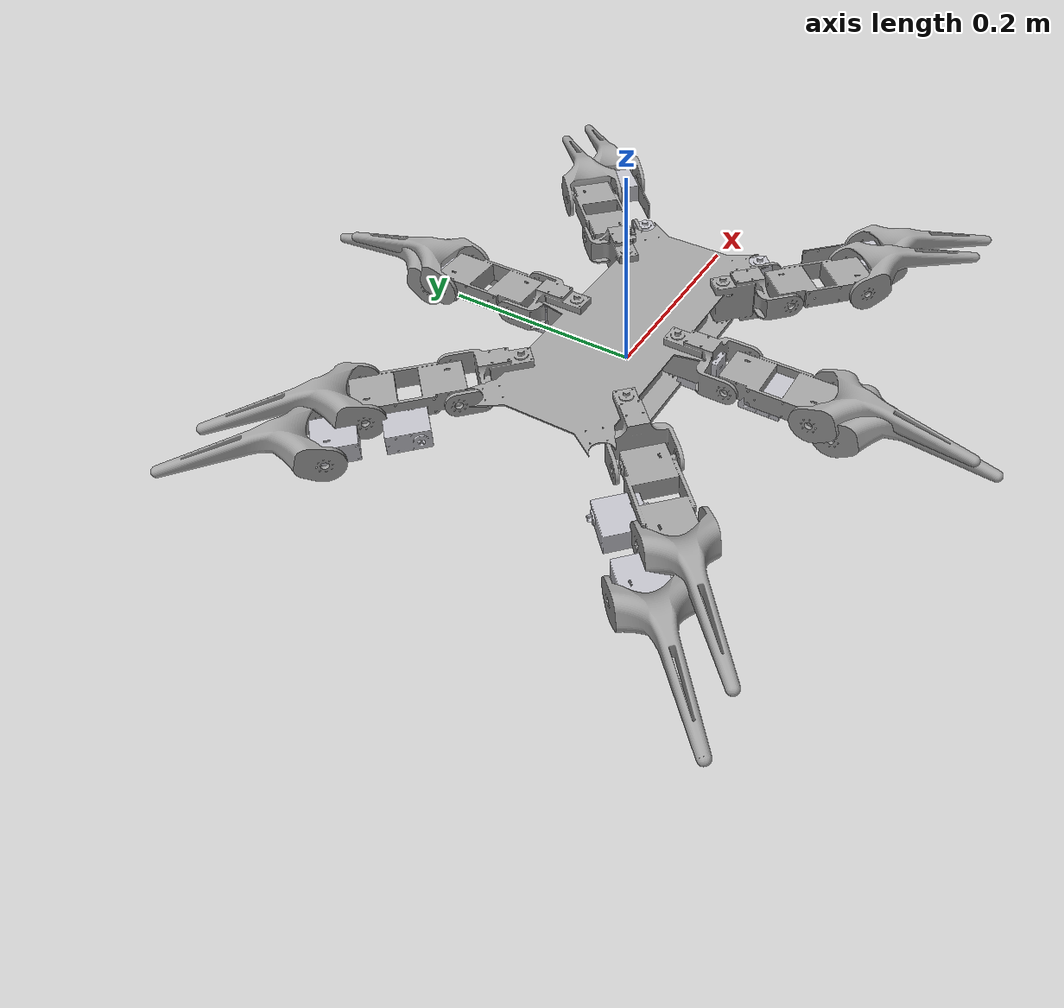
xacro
<?xml version="1.0" ?>
<robot name="spiderrobot" xmlns:xacro="http://www.ros.org/wiki/xacro">

<xacro:include filename="$(find robot_contest)/urdf/materials.xacro" />
<xacro:include filename="$(find robot_contest)/urdf/spiderrobot.trans" />
<xacro:include filename="$(find robot_contest)/urdf/spiderrobot.gazebo" />
<link name="base_link">
  <inertial>
    <origin xyz="3.282245274372618e-08 0.03481866967141663 -0.07599613973394033" rpy="0 0 0"/>
    <mass value="0.32443197759985953"/>
    <inertia ixx="0.002388" iyy="0.005496" izz="0.004327" ixy="-0.0" iyz="0.000796" ixz="-0.0"/>
  </inertial>
  <visual>
    <origin xyz="0 0 0" rpy="0 0 0"/>
    <geometry>
      <mesh filename="package://robot_contest/meshes/base_link.stl" scale="0.001 0.001 0.001"/>
    </geometry>
    <material name="_"/>
  </visual>
  <collision>
    <origin xyz="0 0 0" rpy="0 0 0"/>
    <geometry>
      <mesh filename="package://robot_contest/meshes/base_link.stl" scale="0.001 0.001 0.001"/>
    </geometry>
  </collision>
</link>

<link name="servo1_1">
  <inertial>
    <origin xyz="0.012488449462490642 0.012488246727511476 0.02001368504955774" rpy="0 0 0"/>
    <mass value="0.07069999262512665"/>
    <inertia ixx="1.6e-05" iyy="1.6e-05" izz="1.2e-05" ixy="-3e-06" iyz="-0.0" ixz="-0.0"/>
  </inertial>
  <visual>
    <origin xyz="-0.137126 -0.047626 -0.0015" rpy="0 0 0"/>
    <geometry>
      <mesh filename="package://robot_contest/meshes/servo1_1.stl" scale="0.001 0.001 0.001"/>
    </geometry>
    <material name=""/>
  </visual>
  <collision>
    <origin xyz="-0.137126 -0.047626 -0.0015" rpy="0 0 0"/>
    <geometry>
      <mesh filename="package://robot_contest/meshes/servo1_1.stl" scale="0.001 0.001 0.001"/>
    </geometry>
  </collision>
</link>

<link name="servo2_1">
  <inertial>
    <origin xyz="0.012488449462490642 -0.012488449246155067 0.020013685049556206" rpy="0 0 0"/>
    <mass value="0.07069999262512665"/>
    <inertia ixx="1.6e-05" iyy="1.6e-05" izz="1.2e-05" ixy="3e-06" iyz="0.0" ixz="-0.0"/>
  </inertial>
  <visual>
    <origin xyz="-0.137126 0.047626 -0.0015" rpy="0 0 0"/>
    <geometry>
      <mesh filename="package://robot_contest/meshes/servo2_1.stl" scale="0.001 0.001 0.001"/>
    </geometry>
    <material name=""/>
  </visual>
  <collision>
    <origin xyz="-0.137126 0.047626 -0.0015" rpy="0 0 0"/>
    <geometry>
      <mesh filename="package://robot_contest/meshes/servo2_1.stl" scale="0.001 0.001 0.001"/>
    </geometry>
  </collision>
</link>

<link name="servo3_1">
  <inertial>
    <origin xyz="1.0147565734629952e-07 0.017661611214488462 0.02001368504955727" rpy="0 0 0"/>
    <mass value="0.07069999262512665"/>
    <inertia ixx="1.9e-05" iyy="1.2e-05" izz="1.2e-05" ixy="0.0" iyz="-0.0" ixz="0.0"/>
  </inertial>
  <visual>
    <origin xyz="-0.0 -0.0625 -0.0015" rpy="0 0 0"/>
    <geometry>
      <mesh filename="package://robot_contest/meshes/servo3_1.stl" scale="0.001 0.001 0.001"/>
    </geometry>
    <material name=""/>
  </visual>
  <collision>
    <origin xyz="-0.0 -0.0625 -0.0015" rpy="0 0 0"/>
    <geometry>
      <mesh filename="package://robot_contest/meshes/servo3_1.stl" scale="0.001 0.001 0.001"/>
    </geometry>
  </collision>
</link>

<link name="servo4_1">
  <inertial>
    <origin xyz="1.0147565708061939e-07 -0.017661813733131138 0.02001368504955668" rpy="0 0 0"/>
    <mass value="0.07069999262512665"/>
    <inertia ixx="1.9e-05" iyy="1.2e-05" izz="1.2e-05" ixy="0.0" iyz="0.0" ixz="0.0"/>
  </inertial>
  <visual>
    <origin xyz="-0.0 0.0625 -0.0015" rpy="0 0 0"/>
    <geometry>
      <mesh filename="package://robot_contest/meshes/servo4_1.stl" scale="0.001 0.001 0.001"/>
    </geometry>
    <material name=""/>
  </visual>
  <collision>
    <origin xyz="-0.0 0.0625 -0.0015" rpy="0 0 0"/>
    <geometry>
      <mesh filename="package://robot_contest/meshes/servo4_1.stl" scale="0.001 0.001 0.001"/>
    </geometry>
  </collision>
</link>

<link name="servo5_1">
  <inertial>
    <origin xyz="-0.012488246511175749 0.01248824672751185 0.020013685049556976" rpy="0 0 0"/>
    <mass value="0.07069999262512665"/>
    <inertia ixx="1.6e-05" iyy="1.6e-05" izz="1.2e-05" ixy="3e-06" iyz="-0.0" ixz="0.0"/>
  </inertial>
  <visual>
    <origin xyz="0.137126 -0.047626 -0.0015" rpy="0 0 0"/>
    <geometry>
      <mesh filename="package://robot_contest/meshes/servo5_1.stl" scale="0.001 0.001 0.001"/>
    </geometry>
    <material name=""/>
  </visual>
  <collision>
    <origin xyz="0.137126 -0.047626 -0.0015" rpy="0 0 0"/>
    <geometry>
      <mesh filename="package://robot_contest/meshes/servo5_1.stl" scale="0.001 0.001 0.001"/>
    </geometry>
  </collision>
</link>

<link name="servo6_1">
  <inertial>
    <origin xyz="-0.012488246511176054 -0.012488449246154443 0.02001368504955692" rpy="0 0 0"/>
    <mass value="0.07069999262512665"/>
    <inertia ixx="1.6e-05" iyy="1.6e-05" izz="1.2e-05" ixy="-3e-06" iyz="0.0" ixz="0.0"/>
  </inertial>
  <visual>
    <origin xyz="0.137126 0.047626 -0.0015" rpy="0 0 0"/>
    <geometry>
      <mesh filename="package://robot_contest/meshes/servo6_1.stl" scale="0.001 0.001 0.001"/>
    </geometry>
    <material name=""/>
  </visual>
  <collision>
    <origin xyz="0.137126 0.047626 -0.0015" rpy="0 0 0"/>
    <geometry>
      <mesh filename="package://robot_contest/meshes/servo6_1.stl" scale="0.001 0.001 0.001"/>
    </geometry>
  </collision>
</link>

<link name="cover_1">
  <inertial>
    <origin xyz="-0.15303582986143344 -0.018104806605509255 -0.03691771626412458" rpy="0 0 0"/>
    <mass value="0.32438607775309336"/>
    <inertia ixx="0.001055" iyy="0.004163" izz="0.004326" ixy="0.0" iyz="0.000391" ixz="0.0"/>
  </inertial>
  <visual>
    <origin xyz="-0.153036 -0.052929 -0.0415" rpy="0 0 0"/>
    <geometry>
      <mesh filename="package://robot_contest/meshes/cover_1.stl" scale="0.001 0.001 0.001"/>
    </geometry>
    <material name="_"/>
  </visual>
  <collision>
    <origin xyz="-0.153036 -0.052929 -0.0415" rpy="0 0 0"/>
    <geometry>
      <mesh filename="package://robot_contest/meshes/cover_1.stl" scale="0.001 0.001 0.001"/>
    </geometry>
  </collision>
</link>

<link name="part1_1">
  <inertial>
    <origin xyz="0.008877265681727503 0.008875169024020066 0.01920864547721368" rpy="0 0 0"/>
    <mass value="0.010718837309292628"/>
    <inertia ixx="1e-05" iyy="1e-05" izz="2e-06" ixy="-0.0" iyz="-1e-06" ixz="-1e-06"/>
  </inertial>
  <visual>
    <origin xyz="-0.156571 -0.067071 0.0039" rpy="0 0 0"/>
    <geometry>
      <mesh filename="package://robot_contest/meshes/part1_1.stl" scale="0.001 0.001 0.001"/>
    </geometry>
    <material name="_"/>
  </visual>
  <collision>
    <origin xyz="-0.156571 -0.067071 0.0039" rpy="0 0 0"/>
    <geometry>
      <mesh filename="package://robot_contest/meshes/part1_1.stl" scale="0.001 0.001 0.001"/>
    </geometry>
  </collision>
</link>

<link name="part2_1">
  <inertial>
    <origin xyz="0.008875371758998996 -0.008877265465391831 0.019208645477211746" rpy="0 0 0"/>
    <mass value="0.010718837309292628"/>
    <inertia ixx="1e-05" iyy="1e-05" izz="2e-06" ixy="0.0" iyz="1e-06" ixz="-1e-06"/>
  </inertial>
  <visual>
    <origin xyz="-0.156571 0.067071 0.0039" rpy="0 0 0"/>
    <geometry>
      <mesh filename="package://robot_contest/meshes/part2_1.stl" scale="0.001 0.001 0.001"/>
    </geometry>
    <material name="_"/>
  </visual>
  <collision>
    <origin xyz="-0.156571 0.067071 0.0039" rpy="0 0 0"/>
    <geometry>
      <mesh filename="package://robot_contest/meshes/part2_1.stl" scale="0.001 0.001 0.001"/>
    </geometry>
  </collision>
</link>

<link name="part3_1">
  <inertial>
    <origin xyz="1.4406812617388342e-06 0.012552669650251966 0.019208645477213113" rpy="0 0 0"/>
    <mass value="0.010718837309292628"/>
    <inertia ixx="1.1e-05" iyy="1e-05" izz="2e-06" ixy="0.0" iyz="-1e-06" ixz="0.0"/>
  </inertial>
  <visual>
    <origin xyz="-0.0 -0.09 0.0039" rpy="0 0 0"/>
    <geometry>
      <mesh filename="package://robot_contest/meshes/part3_1.stl" scale="0.001 0.001 0.001"/>
    </geometry>
    <material name="_"/>
  </visual>
  <collision>
    <origin xyz="-0.0 -0.09 0.0039" rpy="0 0 0"/>
    <geometry>
      <mesh filename="package://robot_contest/meshes/part3_1.stl" scale="0.001 0.001 0.001"/>
    </geometry>
  </collision>
</link>

<link name="part4_1">
  <inertial>
    <origin xyz="-1.2377299472739092e-06 -0.012552872168894627 0.01920864547721229" rpy="0 0 0"/>
    <mass value="0.010718837309292628"/>
    <inertia ixx="1.1e-05" iyy="1e-05" izz="2e-06" ixy="0.0" iyz="1e-06" ixz="-0.0"/>
  </inertial>
  <visual>
    <origin xyz="-0.0 0.09 0.0039" rpy="0 0 0"/>
    <geometry>
      <mesh filename="package://robot_contest/meshes/part4_1.stl" scale="0.001 0.001 0.001"/>
    </geometry>
    <material name="_"/>
  </visual>
  <collision>
    <origin xyz="-0.0 0.09 0.0039" rpy="0 0 0"/>
    <geometry>
      <mesh filename="package://robot_contest/meshes/part4_1.stl" scale="0.001 0.001 0.001"/>
    </geometry>
  </collision>
</link>

<link name="part5_1">
  <inertial>
    <origin xyz="-0.008875168807684214 0.008877062946748837 0.019208645477212693" rpy="0 0 0"/>
    <mass value="0.010718837309292628"/>
    <inertia ixx="1e-05" iyy="1e-05" izz="2e-06" ixy="0.0" iyz="-1e-06" ixz="1e-06"/>
  </inertial>
  <visual>
    <origin xyz="0.156571 -0.067071 0.0039" rpy="0 0 0"/>
    <geometry>
      <mesh filename="package://robot_contest/meshes/part5_1.stl" scale="0.001 0.001 0.001"/>
    </geometry>
    <material name="_"/>
  </visual>
  <collision>
    <origin xyz="0.156571 -0.067071 0.0039" rpy="0 0 0"/>
    <geometry>
      <mesh filename="package://robot_contest/meshes/part5_1.stl" scale="0.001 0.001 0.001"/>
    </geometry>
  </collision>
</link>

<link name="part6_1">
  <inertial>
    <origin xyz="-0.008877062730412832 -0.008875371542662686 0.019208645477212644" rpy="0 0 0"/>
    <mass value="0.010718837309292628"/>
    <inertia ixx="1e-05" iyy="1e-05" izz="2e-06" ixy="-0.0" iyz="1e-06" ixz="1e-06"/>
  </inertial>
  <visual>
    <origin xyz="0.156571 0.067071 0.0039" rpy="0 0 0"/>
    <geometry>
      <mesh filename="package://robot_contest/meshes/part6_1.stl" scale="0.001 0.001 0.001"/>
    </geometry>
    <material name="_"/>
  </visual>
  <collision>
    <origin xyz="0.156571 0.067071 0.0039" rpy="0 0 0"/>
    <geometry>
      <mesh filename="package://robot_contest/meshes/part6_1.stl" scale="0.001 0.001 0.001"/>
    </geometry>
  </collision>
</link>

<link name="part7_1">
  <inertial>
    <origin xyz="0.007930031540899107 0.0075518428650224595 -0.00583266079439447" rpy="0 0 0"/>
    <mass value="0.010718837309292628"/>
    <inertia ixx="7e-06" iyy="5e-06" izz="1.1e-05" ixy="4e-06" iyz="-0.0" ixz="0.0"/>
  </inertial>
  <visual>
    <origin xyz="-0.169063 -0.087813 -0.026709" rpy="0 0 0"/>
    <geometry>
      <mesh filename="package://robot_contest/meshes/part7_1.stl" scale="0.001 0.001 0.001"/>
    </geometry>
    <material name="_"/>
  </visual>
  <collision>
    <origin xyz="-0.169063 -0.087813 -0.026709" rpy="0 0 0"/>
    <geometry>
      <mesh filename="package://robot_contest/meshes/part7_1.stl" scale="0.001 0.001 0.001"/>
    </geometry>
  </collision>
</link>

<link name="part8_1">
  <inertial>
    <origin xyz="0.007552045600001611 -0.007930031324563533 -0.005832660794396784" rpy="0 0 0"/>
    <mass value="0.010718837309292628"/>
    <inertia ixx="5e-06" iyy="7e-06" izz="1.1e-05" ixy="-4e-06" iyz="-0.0" ixz="-0.0"/>
  </inertial>
  <visual>
    <origin xyz="-0.177313 0.079563 -0.026709" rpy="0 0 0"/>
    <geometry>
      <mesh filename="package://robot_contest/meshes/part8_1.stl" scale="0.001 0.001 0.001"/>
    </geometry>
    <material name="_"/>
  </visual>
  <collision>
    <origin xyz="-0.177313 0.079563 -0.026709" rpy="0 0 0"/>
    <geometry>
      <mesh filename="package://robot_contest/meshes/part8_1.stl" scale="0.001 0.001 0.001"/>
    </geometry>
  </collision>
</link>

<link name="part9_1">
  <inertial>
    <origin xyz="-0.011400253047129822 0.010947127831105685 -0.0058326607943951884" rpy="0 0 0"/>
    <mass value="0.010718837309292628"/>
    <inertia ixx="2e-06" iyy="1e-05" izz="1.1e-05" ixy="1e-06" iyz="-0.0" ixz="0.0"/>
  </inertial>
  <visual>
    <origin xyz="-0.005834 -0.1135 -0.026709" rpy="0 0 0"/>
    <geometry>
      <mesh filename="package://robot_contest/meshes/part9_1.stl" scale="0.001 0.001 0.001"/>
    </geometry>
    <material name="_"/>
  </visual>
  <collision>
    <origin xyz="-0.005834 -0.1135 -0.026709" rpy="0 0 0"/>
    <geometry>
      <mesh filename="package://robot_contest/meshes/part9_1.stl" scale="0.001 0.001 0.001"/>
    </geometry>
  </collision>
</link>

<link name="part10_1">
  <inertial>
    <origin xyz="-0.00026754400155569024 -0.01094733034974836 -0.005832660794396226" rpy="0 0 0"/>
    <mass value="0.010718837309292628"/>
    <inertia ixx="2e-06" iyy="1e-05" izz="1.1e-05" ixy="1e-06" iyz="0.0" ixz="-0.0"/>
  </inertial>
  <visual>
    <origin xyz="-0.005834 0.1135 -0.026709" rpy="0 0 0"/>
    <geometry>
      <mesh filename="package://robot_contest/meshes/part10_1.stl" scale="0.001 0.001 0.001"/>
    </geometry>
    <material name="_"/>
  </visual>
  <collision>
    <origin xyz="-0.005834 0.1135 -0.026709" rpy="0 0 0"/>
    <geometry>
      <mesh filename="package://robot_contest/meshes/part10_1.stl" scale="0.001 0.001 0.001"/>
    </geometry>
  </collision>
</link>

<link name="part11_1">
  <inertial>
    <origin xyz="-0.00755184264868658 0.00792982880592033 -0.0058326607943957505" rpy="0 0 0"/>
    <mass value="0.010718837309292628"/>
    <inertia ixx="5e-06" iyy="7e-06" izz="1.1e-05" ixy="-4e-06" iyz="0.0" ixz="0.0"/>
  </inertial>
  <visual>
    <origin xyz="0.177313 -0.079563 -0.026709" rpy="0 0 0"/>
    <geometry>
      <mesh filename="package://robot_contest/meshes/part11_1.stl" scale="0.001 0.001 0.001"/>
    </geometry>
    <material name="_"/>
  </visual>
  <collision>
    <origin xyz="0.177313 -0.079563 -0.026709" rpy="0 0 0"/>
    <geometry>
      <mesh filename="package://robot_contest/meshes/part11_1.stl" scale="0.001 0.001 0.001"/>
    </geometry>
  </collision>
</link>

<link name="part12_1">
  <inertial>
    <origin xyz="-0.007929828589584353 -0.007552045383665287 -0.0058326607943957505" rpy="0 0 0"/>
    <mass value="0.010718837309292628"/>
    <inertia ixx="7e-06" iyy="5e-06" izz="1.1e-05" ixy="4e-06" iyz="0.0" ixz="-0.0"/>
  </inertial>
  <visual>
    <origin xyz="0.169063 0.087813 -0.026709" rpy="0 0 0"/>
    <geometry>
      <mesh filename="package://robot_contest/meshes/part12_1.stl" scale="0.001 0.001 0.001"/>
    </geometry>
    <material name="_"/>
  </visual>
  <collision>
    <origin xyz="0.169063 0.087813 -0.026709" rpy="0 0 0"/>
    <geometry>
      <mesh filename="package://robot_contest/meshes/part12_1.stl" scale="0.001 0.001 0.001"/>
    </geometry>
  </collision>
</link>

<link name="servo7_1">
  <inertial>
    <origin xyz="0.025704526357907126 -0.011790913436240488 1.4085954624931674e-15" rpy="0 0 0"/>
    <mass value="0.07069999262512665"/>
    <inertia ixx="1.2e-05" iyy="1.2e-05" izz="1.9e-05" ixy="0.0" iyz="-0.0" ixz="-0.0"/>
  </inertial>
  <visual>
    <origin xyz="-0.171509 -0.118601 -0.020875" rpy="0 0 0"/>
    <geometry>
      <mesh filename="package://robot_contest/meshes/servo7_1.stl" scale="0.001 0.001 0.001"/>
    </geometry>
    <material name=""/>
  </visual>
  <collision>
    <origin xyz="-0.171509 -0.118601 -0.020875" rpy="0 0 0"/>
    <geometry>
      <mesh filename="package://robot_contest/meshes/servo7_1.stl" scale="0.001 0.001 0.001"/>
    </geometry>
  </collision>
</link>

<link name="servo8_1">
  <inertial>
    <origin xyz="0.025704526357907154 0.011791710917596607 -1.366962099069724e-15" rpy="0 0 0"/>
    <mass value="0.07069999262512665"/>
    <inertia ixx="1.2e-05" iyy="1.2e-05" izz="1.9e-05" ixy="-0.0" iyz="-0.0" ixz="-0.0"/>
  </inertial>
  <visual>
    <origin xyz="-0.171509 0.118602 -0.020875" rpy="0 0 0"/>
    <geometry>
      <mesh filename="package://robot_contest/meshes/servo8_1.stl" scale="0.001 0.001 0.001"/>
    </geometry>
    <material name=""/>
  </visual>
  <collision>
    <origin xyz="-0.171509 0.118602 -0.020875" rpy="0 0 0"/>
    <geometry>
      <mesh filename="package://robot_contest/meshes/servo8_1.stl" scale="0.001 0.001 0.001"/>
    </geometry>
  </collision>
</link>

<link name="servo9_1">
  <inertial>
    <origin xyz="0.026513786525214435 0.009838186266869442 5.793976409762536e-16" rpy="0 0 0"/>
    <mass value="0.07069999262512665"/>
    <inertia ixx="1.2e-05" iyy="1.2e-05" izz="1.9e-05" ixy="0.0" iyz="-0.0" ixz="-0.0"/>
  </inertial>
  <visual>
    <origin xyz="0.025875 -0.137 -0.020875" rpy="0 0 0"/>
    <geometry>
      <mesh filename="package://robot_contest/meshes/servo9_1.stl" scale="0.001 0.001 0.001"/>
    </geometry>
    <material name=""/>
  </visual>
  <collision>
    <origin xyz="0.025875 -0.137 -0.020875" rpy="0 0 0"/>
    <geometry>
      <mesh filename="package://robot_contest/meshes/servo9_1.stl" scale="0.001 0.001 0.001"/>
    </geometry>
  </collision>
</link>

<link name="servo10_1">
  <inertial>
    <origin xyz="0.026513786525213995 -0.009838388785511742 -5.585809592645319e-16" rpy="0 0 0"/>
    <mass value="0.07069999262512665"/>
    <inertia ixx="1.2e-05" iyy="1.2e-05" izz="1.9e-05" ixy="-0.0" iyz="-0.0" ixz="0.0"/>
  </inertial>
  <visual>
    <origin xyz="0.025875 0.137 -0.020875" rpy="0 0 0"/>
    <geometry>
      <mesh filename="package://robot_contest/meshes/servo10_1.stl" scale="0.001 0.001 0.001"/>
    </geometry>
    <material name=""/>
  </visual>
  <collision>
    <origin xyz="0.025875 0.137 -0.020875" rpy="0 0 0"/>
    <geometry>
      <mesh filename="package://robot_contest/meshes/servo10_1.stl" scale="0.001 0.001 0.001"/>
    </geometry>
  </collision>
</link>

<link name="servo11_1">
  <inertial>
    <origin xyz="0.011790913652576313 0.025704323622928404 -2.7755575615628914e-17" rpy="0 0 0"/>
    <mass value="0.07069999262512665"/>
    <inertia ixx="1.2e-05" iyy="1.2e-05" izz="1.9e-05" ixy="-0.0" iyz="-0.0" ixz="-0.0"/>
  </inertial>
  <visual>
    <origin xyz="0.208101 -0.082009 -0.020875" rpy="0 0 0"/>
    <geometry>
      <mesh filename="package://robot_contest/meshes/servo11_1.stl" scale="0.001 0.001 0.001"/>
    </geometry>
    <material name=""/>
  </visual>
  <collision>
    <origin xyz="0.208101 -0.082009 -0.020875" rpy="0 0 0"/>
    <geometry>
      <mesh filename="package://robot_contest/meshes/servo11_1.stl" scale="0.001 0.001 0.001"/>
    </geometry>
  </collision>
</link>

<link name="servo12_1">
  <inertial>
    <origin xyz="0.011790913652575896 -0.02570452614157083 -2.42861286636753e-17" rpy="0 0 0"/>
    <mass value="0.07069999262512665"/>
    <inertia ixx="1.2e-05" iyy="1.2e-05" izz="1.9e-05" ixy="0.0" iyz="-0.0" ixz="-0.0"/>
  </inertial>
  <visual>
    <origin xyz="0.208101 0.082009 -0.020875" rpy="0 0 0"/>
    <geometry>
      <mesh filename="package://robot_contest/meshes/servo12_1.stl" scale="0.001 0.001 0.001"/>
    </geometry>
    <material name=""/>
  </visual>
  <collision>
    <origin xyz="0.208101 0.082009 -0.020875" rpy="0 0 0"/>
    <geometry>
      <mesh filename="package://robot_contest/meshes/servo12_1.stl" scale="0.001 0.001 0.001"/>
    </geometry>
  </collision>
</link>

<link name="part13_1">
  <inertial>
    <origin xyz="0.057132069906387195 -0.03834292511619296 3.9216201648539784e-07" rpy="0 0 0"/>
    <mass value="0.12025967261023773"/>
    <inertia ixx="8.8e-05" iyy="8.6e-05" izz="0.000166" ixy="-4.5e-05" iyz="0.0" ixz="-0.0"/>
  </inertial>
  <visual>
    <origin xyz="-0.19555 -0.133451 -0.020875" rpy="0 0 0"/>
    <geometry>
      <mesh filename="package://robot_contest/meshes/part13_1.stl" scale="0.001 0.001 0.001"/>
    </geometry>
    <material name="_"/>
  </visual>
  <collision>
    <origin xyz="-0.19555 -0.133451 -0.020875" rpy="0 0 0"/>
    <geometry>
      <mesh filename="package://robot_contest/meshes/part13_1.stl" scale="0.001 0.001 0.001"/>
    </geometry>
  </collision>
</link>

<link name="part14_1">
  <inertial>
    <origin xyz="-0.03940277032397255 -0.058192117632806906 3.921620186468633e-07" rpy="0 0 0"/>
    <mass value="0.12025967261023773"/>
    <inertia ixx="8.6e-05" iyy="8.8e-05" izz="0.000166" ixy="4.5e-05" iyz="0.0" ixz="0.0"/>
  </inertial>
  <visual>
    <origin xyz="-0.19555 0.133451 -0.020875" rpy="0 0 0"/>
    <geometry>
      <mesh filename="package://robot_contest/meshes/part14_1.stl" scale="0.001 0.001 0.001"/>
    </geometry>
    <material name="_"/>
  </visual>
  <collision>
    <origin xyz="-0.19555 0.133451 -0.020875" rpy="0 0 0"/>
    <geometry>
      <mesh filename="package://robot_contest/meshes/part14_1.stl" scale="0.001 0.001 0.001"/>
    </geometry>
  </collision>
</link>

<link name="part15_1">
  <inertial>
    <origin xyz="0.06751054162330213 0.01328579774012012 3.921620219150823e-07" rpy="0 0 0"/>
    <mass value="0.12025967261023773"/>
    <inertia ixx="0.000132" iyy="4.2e-05" izz="0.000166" ixy="1e-06" iyz="0.0" ixz="-0.0"/>
  </inertial>
  <visual>
    <origin xyz="0.019375 -0.1645 -0.020875" rpy="0 0 0"/>
    <geometry>
      <mesh filename="package://robot_contest/meshes/part15_1.stl" scale="0.001 0.001 0.001"/>
    </geometry>
    <material name="_"/>
  </visual>
  <collision>
    <origin xyz="0.019375 -0.1645 -0.020875" rpy="0 0 0"/>
    <geometry>
      <mesh filename="package://robot_contest/meshes/part15_1.stl" scale="0.001 0.001 0.001"/>
    </geometry>
  </collision>
</link>

<link name="part16_1">
  <inertial>
    <origin xyz="-0.06901033867198803 -0.013286000258761477 3.921620202601561e-07" rpy="0 0 0"/>
    <mass value="0.12025967261023773"/>
    <inertia ixx="0.000132" iyy="4.2e-05" izz="0.000166" ixy="1e-06" iyz="-0.0" ixz="0.0"/>
  </inertial>
  <visual>
    <origin xyz="0.019375 0.1645 -0.020875" rpy="0 0 0"/>
    <geometry>
      <mesh filename="package://robot_contest/meshes/part16_1.stl" scale="0.001 0.001 0.001"/>
    </geometry>
    <material name="_"/>
  </visual>
  <collision>
    <origin xyz="0.019375 0.1645 -0.020875" rpy="0 0 0"/>
    <geometry>
      <mesh filename="package://robot_contest/meshes/part16_1.stl" scale="0.001 0.001 0.001"/>
    </geometry>
  </collision>
</link>

<link name="part17_1">
  <inertial>
    <origin xyz="0.03834292533252934 0.05713186717140509 3.921620210269039e-07" rpy="0 0 0"/>
    <mass value="0.12025967261023773"/>
    <inertia ixx="8.6e-05" iyy="8.8e-05" izz="0.000166" ixy="4.5e-05" iyz="-0.0" ixz="-0.0"/>
  </inertial>
  <visual>
    <origin xyz="0.222951 -0.10605 -0.020875" rpy="0 0 0"/>
    <geometry>
      <mesh filename="package://robot_contest/meshes/part17_1.stl" scale="0.001 0.001 0.001"/>
    </geometry>
    <material name="_"/>
  </visual>
  <collision>
    <origin xyz="0.222951 -0.10605 -0.020875" rpy="0 0 0"/>
    <geometry>
      <mesh filename="package://robot_contest/meshes/part17_1.stl" scale="0.001 0.001 0.001"/>
    </geometry>
  </collision>
</link>

<link name="part18_1">
  <inertial>
    <origin xyz="-0.05819191489782782 0.039402770540309315 3.9216202103731224e-07" rpy="0 0 0"/>
    <mass value="0.12025967261023773"/>
    <inertia ixx="8.8e-05" iyy="8.6e-05" izz="0.000166" ixy="-4.5e-05" iyz="-0.0" ixz="0.0"/>
  </inertial>
  <visual>
    <origin xyz="0.222951 0.10605 -0.020875" rpy="0 0 0"/>
    <geometry>
      <mesh filename="package://robot_contest/meshes/part18_1.stl" scale="0.001 0.001 0.001"/>
    </geometry>
    <material name="_"/>
  </visual>
  <collision>
    <origin xyz="0.222951 0.10605 -0.020875" rpy="0 0 0"/>
    <geometry>
      <mesh filename="package://robot_contest/meshes/part18_1.stl" scale="0.001 0.001 0.001"/>
    </geometry>
  </collision>
</link>

<link name="part19_1">
  <inertial>
    <origin xyz="-0.03852088697722983 0.05695393562242289 -0.007499607837977276" rpy="0 0 0"/>
    <mass value="0.12025967261023773"/>
    <inertia ixx="8.8e-05" iyy="8.6e-05" izz="0.000166" ixy="-4.5e-05" iyz="-0.0" ixz="0.0"/>
  </inertial>
  <visual>
    <origin xyz="-0.223835 -0.105166 -0.028375" rpy="0 0 0"/>
    <geometry>
      <mesh filename="package://robot_contest/meshes/part19_1.stl" scale="0.001 0.001 0.001"/>
    </geometry>
    <material name="_"/>
  </visual>
  <collision>
    <origin xyz="-0.223835 -0.105166 -0.028375" rpy="0 0 0"/>
    <geometry>
      <mesh filename="package://robot_contest/meshes/part19_1.stl" scale="0.001 0.001 0.001"/>
    </geometry>
  </collision>
</link>

<link name="part20_1">
  <inertial>
    <origin xyz="0.06862095325312759 0.02897470208928979 -0.007499607837979996" rpy="0 0 0"/>
    <mass value="0.12025967261023773"/>
    <inertia ixx="8.6e-05" iyy="8.8e-05" izz="0.000166" ixy="4.5e-05" iyz="-0.0" ixz="-0.0"/>
  </inertial>
  <visual>
    <origin xyz="-0.213228 0.09456 -0.028375" rpy="0 0 0"/>
    <geometry>
      <mesh filename="package://robot_contest/meshes/part20_1.stl" scale="0.001 0.001 0.001"/>
    </geometry>
    <material name="_"/>
  </visual>
  <collision>
    <origin xyz="-0.213228 0.09456 -0.028375" rpy="0 0 0"/>
    <geometry>
      <mesh filename="package://robot_contest/meshes/part20_1.stl" scale="0.001 0.001 0.001"/>
    </geometry>
  </collision>
</link>

<link name="part21_1">
  <inertial>
    <origin xyz="-0.06751033867198804 0.028033999741238408 -0.007499607837978341" rpy="0 0 0"/>
    <mass value="0.12025967261023773"/>
    <inertia ixx="0.000132" iyy="4.2e-05" izz="0.000166" ixy="1e-06" iyz="-0.0" ixz="0.0"/>
  </inertial>
  <visual>
    <origin xyz="-0.020625 -0.1495 -0.028375" rpy="0 0 0"/>
    <geometry>
      <mesh filename="package://robot_contest/meshes/part21_1.stl" scale="0.001 0.001 0.001"/>
    </geometry>
    <material name="_"/>
  </visual>
  <collision>
    <origin xyz="-0.020625 -0.1495 -0.028375" rpy="0 0 0"/>
    <geometry>
      <mesh filename="package://robot_contest/meshes/part21_1.stl" scale="0.001 0.001 0.001"/>
    </geometry>
  </collision>
</link>

<link name="part22_1">
  <inertial>
    <origin xyz="0.06901054162330238 -0.028034202259880597 -0.007499607837979771" rpy="0 0 0"/>
    <mass value="0.12025967261023773"/>
    <inertia ixx="0.000132" iyy="4.2e-05" izz="0.000166" ixy="1e-06" iyz="0.0" ixz="-0.0"/>
  </inertial>
  <visual>
    <origin xyz="-0.020625 0.1495 -0.028375" rpy="0 0 0"/>
    <geometry>
      <mesh filename="package://robot_contest/meshes/part22_1.stl" scale="0.001 0.001 0.001"/>
    </geometry>
    <material name="_"/>
  </visual>
  <collision>
    <origin xyz="-0.020625 0.1495 -0.028375" rpy="0 0 0"/>
    <geometry>
      <mesh filename="package://robot_contest/meshes/part22_1.stl" scale="0.001 0.001 0.001"/>
    </geometry>
  </collision>
</link>

<link name="part23_1">
  <inertial>
    <origin xyz="-0.06755993540608735 -0.027914089712207935 -0.007499607837979202" rpy="0 0 0"/>
    <mass value="0.12025967261023773"/>
    <inertia ixx="8.6e-05" iyy="8.8e-05" izz="0.000166" ixy="4.5e-05" iyz="0.0" ixz="0.0"/>
  </inertial>
  <visual>
    <origin xyz="0.18406 -0.123728 -0.028375" rpy="0 0 0"/>
    <geometry>
      <mesh filename="package://robot_contest/meshes/part23_1.stl" scale="0.001 0.001 0.001"/>
    </geometry>
    <material name="_"/>
  </visual>
  <collision>
    <origin xyz="0.18406 -0.123728 -0.028375" rpy="0 0 0"/>
    <geometry>
      <mesh filename="package://robot_contest/meshes/part23_1.stl" scale="0.001 0.001 0.001"/>
    </geometry>
  </collision>
</link>

<link name="part24_1">
  <inertial>
    <origin xyz="0.02897490482426915 -0.06862095303679103 -0.007499607837979087" rpy="0 0 0"/>
    <mass value="0.12025967261023773"/>
    <inertia ixx="8.8e-05" iyy="8.6e-05" izz="0.000166" ixy="-4.5e-05" iyz="0.0" ixz="-0.0"/>
  </inertial>
  <visual>
    <origin xyz="0.18406 0.123728 -0.028375" rpy="0 0 0"/>
    <geometry>
      <mesh filename="package://robot_contest/meshes/part24_1.stl" scale="0.001 0.001 0.001"/>
    </geometry>
    <material name="_"/>
  </visual>
  <collision>
    <origin xyz="0.18406 0.123728 -0.028375" rpy="0 0 0"/>
    <geometry>
      <mesh filename="package://robot_contest/meshes/part24_1.stl" scale="0.001 0.001 0.001"/>
    </geometry>
  </collision>
</link>

<link name="servo13_1">
  <inertial>
    <origin xyz="-0.0016633434287527116 0.02664092394247075 1.9845236565174673e-15" rpy="0 0 0"/>
    <mass value="0.07069999262512665"/>
    <inertia ixx="1.2e-05" iyy="1.2e-05" izz="1.9e-05" ixy="0.0" iyz="0.0" ixz="0.0"/>
  </inertial>
  <visual>
    <origin xyz="-0.242446 -0.123777 -0.020875" rpy="0 0 0"/>
    <geometry>
      <mesh filename="package://robot_contest/meshes/servo13_1.stl" scale="0.001 0.001 0.001"/>
    </geometry>
    <material name=""/>
  </visual>
  <collision>
    <origin xyz="-0.242446 -0.123777 -0.020875" rpy="0 0 0"/>
    <geometry>
      <mesh filename="package://robot_contest/meshes/servo13_1.stl" scale="0.001 0.001 0.001"/>
    </geometry>
  </collision>
</link>

<link name="servo14_1">
  <inertial>
    <origin xyz="-0.0016633434287518234 -0.02664012646111391 -1.8006429680639258e-15" rpy="0 0 0"/>
    <mass value="0.07069999262512665"/>
    <inertia ixx="1.2e-05" iyy="1.2e-05" izz="1.9e-05" ixy="-0.0" iyz="-0.0" ixz="0.0"/>
  </inertial>
  <visual>
    <origin xyz="-0.242446 0.123778 -0.020875" rpy="0 0 0"/>
    <geometry>
      <mesh filename="package://robot_contest/meshes/servo14_1.stl" scale="0.001 0.001 0.001"/>
    </geometry>
    <material name=""/>
  </visual>
  <collision>
    <origin xyz="-0.242446 0.123778 -0.020875" rpy="0 0 0"/>
    <geometry>
      <mesh filename="package://robot_contest/meshes/servo14_1.stl" scale="0.001 0.001 0.001"/>
    </geometry>
  </collision>
</link>

<link name="servo15_1">
  <inertial>
    <origin xyz="-0.02001358357389976 0.017661611214488893 7.042977312465837e-16" rpy="0 0 0"/>
    <mass value="0.07069999262512665"/>
    <inertia ixx="1.2e-05" iyy="1.2e-05" izz="1.9e-05" ixy="0.0" iyz="0.0" ixz="0.0"/>
  </inertial>
  <visual>
    <origin xyz="-0.020625 -0.19082 -0.020875" rpy="0 0 0"/>
    <geometry>
      <mesh filename="package://robot_contest/meshes/servo15_1.stl" scale="0.001 0.001 0.001"/>
    </geometry>
    <material name=""/>
  </visual>
  <collision>
    <origin xyz="-0.020625 -0.19082 -0.020875" rpy="0 0 0"/>
    <geometry>
      <mesh filename="package://robot_contest/meshes/servo15_1.stl" scale="0.001 0.001 0.001"/>
    </geometry>
  </collision>
</link>

<link name="servo16_1">
  <inertial>
    <origin xyz="-0.020013583573899388 -0.01766181373313125 -8.187894806610529e-16" rpy="0 0 0"/>
    <mass value="0.07069999262512665"/>
    <inertia ixx="1.2e-05" iyy="1.2e-05" izz="1.9e-05" ixy="-0.0" iyz="0.0" ixz="-0.0"/>
  </inertial>
  <visual>
    <origin xyz="-0.020625 0.19082 -0.020875" rpy="0 0 0"/>
    <geometry>
      <mesh filename="package://robot_contest/meshes/servo16_1.stl" scale="0.001 0.001 0.001"/>
    </geometry>
    <material name=""/>
  </visual>
  <collision>
    <origin xyz="-0.020625 0.19082 -0.020875" rpy="0 0 0"/>
    <geometry>
      <mesh filename="package://robot_contest/meshes/servo16_1.stl" scale="0.001 0.001 0.001"/>
    </geometry>
  </collision>
</link>

<link name="servo17_1">
  <inertial>
    <origin xyz="-0.026640923726134302 -0.0016635461637316273 -4.5102810375396984e-17" rpy="0 0 0"/>
    <mass value="0.07069999262512665"/>
    <inertia ixx="1.2e-05" iyy="1.2e-05" izz="1.9e-05" ixy="-0.0" iyz="0.0" ixz="-0.0"/>
  </inertial>
  <visual>
    <origin xyz="0.213277 -0.152946 -0.020875" rpy="0 0 0"/>
    <geometry>
      <mesh filename="package://robot_contest/meshes/servo17_1.stl" scale="0.001 0.001 0.001"/>
    </geometry>
    <material name=""/>
  </visual>
  <collision>
    <origin xyz="0.213277 -0.152946 -0.020875" rpy="0 0 0"/>
    <geometry>
      <mesh filename="package://robot_contest/meshes/servo17_1.stl" scale="0.001 0.001 0.001"/>
    </geometry>
  </collision>
</link>

<link name="servo18_1">
  <inertial>
    <origin xyz="-0.02664092372613458 0.0016633436450886052 -3.469446951953614e-18" rpy="0 0 0"/>
    <mass value="0.07069999262512665"/>
    <inertia ixx="1.2e-05" iyy="1.2e-05" izz="1.9e-05" ixy="0.0" iyz="-0.0" ixz="0.0"/>
  </inertial>
  <visual>
    <origin xyz="0.213277 0.152946 -0.020875" rpy="0 0 0"/>
    <geometry>
      <mesh filename="package://robot_contest/meshes/servo18_1.stl" scale="0.001 0.001 0.001"/>
    </geometry>
    <material name=""/>
  </visual>
  <collision>
    <origin xyz="0.213277 0.152946 -0.020875" rpy="0 0 0"/>
    <geometry>
      <mesh filename="package://robot_contest/meshes/servo18_1.stl" scale="0.001 0.001 0.001"/>
    </geometry>
  </collision>
</link>

<link name="part25_1">
  <inertial>
    <origin xyz="0.0017361935097957026 0.044915648494241484 0.008899740383932198" rpy="0 0 0"/>
    <mass value="0.06576925216163401"/>
    <inertia ixx="4.5e-05" iyy="7e-05" izz="0.000103" ixy="-1.7e-05" iyz="1e-06" ixz="-4e-06"/>
  </inertial>
  <visual>
    <origin xyz="-0.26571 -0.139404 -0.020875" rpy="0 0 0"/>
    <geometry>
      <mesh filename="package://robot_contest/meshes/part25_1.stl" scale="0.001 0.001 0.001"/>
    </geometry>
    <material name="_"/>
  </visual>
  <collision>
    <origin xyz="-0.26571 -0.139404 -0.020875" rpy="0 0 0"/>
    <geometry>
      <mesh filename="package://robot_contest/meshes/part25_1.stl" scale="0.001 0.001 0.001"/>
    </geometry>
  </collision>
</link>

<link name="part26_1">
  <inertial>
    <origin xyz="0.009877618182187353 -0.03677342634049424 0.008899740383927643" rpy="0 0 0"/>
    <mass value="0.06576925216163401"/>
    <inertia ixx="7e-05" iyy="4.5e-05" izz="0.000103" ixy="1.7e-05" iyz="4e-06" ixz="1e-06"/>
  </inertial>
  <visual>
    <origin xyz="-0.26571 0.139405 -0.020875" rpy="0 0 0"/>
    <geometry>
      <mesh filename="package://robot_contest/meshes/part26_1.stl" scale="0.001 0.001 0.001"/>
    </geometry>
    <material name="_"/>
  </visual>
  <collision>
    <origin xyz="-0.26571 0.139405 -0.020875" rpy="0 0 0"/>
    <geometry>
      <mesh filename="package://robot_contest/meshes/part26_1.stl" scale="0.001 0.001 0.001"/>
    </geometry>
  </collision>
</link>

<link name="part27_1">
  <inertial>
    <origin xyz="-0.03053175511870967 0.03298771831863015 0.008899740383930703" rpy="0 0 0"/>
    <mass value="0.06576925216163401"/>
    <inertia ixx="7.4e-05" iyy="4e-05" izz="0.000103" ixy="-1.2e-05" iyz="-2e-06" ixz="-3e-06"/>
  </inertial>
  <visual>
    <origin xyz="-0.026025 -0.21832 -0.020875" rpy="0 0 0"/>
    <geometry>
      <mesh filename="package://robot_contest/meshes/part27_1.stl" scale="0.001 0.001 0.001"/>
    </geometry>
    <material name="_"/>
  </visual>
  <collision>
    <origin xyz="-0.026025 -0.21832 -0.020875" rpy="0 0 0"/>
    <geometry>
      <mesh filename="package://robot_contest/meshes/part27_1.stl" scale="0.001 0.001 0.001"/>
    </geometry>
  </collision>
</link>

<link name="part28_1">
  <inertial>
    <origin xyz="-0.019018041929975315 -0.032987920837272505 0.00889974038392878" rpy="0 0 0"/>
    <mass value="0.06576925216163401"/>
    <inertia ixx="7.4e-05" iyy="4e-05" izz="0.000103" ixy="-1.2e-05" iyz="2e-06" ixz="3e-06"/>
  </inertial>
  <visual>
    <origin xyz="-0.026025 0.21832 -0.020875" rpy="0 0 0"/>
    <geometry>
      <mesh filename="package://robot_contest/meshes/part28_1.stl" scale="0.001 0.001 0.001"/>
    </geometry>
    <material name="_"/>
  </visual>
  <collision>
    <origin xyz="-0.026025 0.21832 -0.020875" rpy="0 0 0"/>
    <geometry>
      <mesh filename="package://robot_contest/meshes/part28_1.stl" scale="0.001 0.001 0.001"/>
    </geometry>
  </collision>
</link>

<link name="part29_1">
  <inertial>
    <origin xyz="-0.04491564827790512 0.00173699077481701 0.008899740383929485" rpy="0 0 0"/>
    <mass value="0.06576925216163401"/>
    <inertia ixx="7e-05" iyy="4.5e-05" izz="0.000103" ixy="1.7e-05" iyz="-4e-06" ixz="-1e-06"/>
  </inertial>
  <visual>
    <origin xyz="0.228904 -0.176209 -0.020875" rpy="0 0 0"/>
    <geometry>
      <mesh filename="package://robot_contest/meshes/part29_1.stl" scale="0.001 0.001 0.001"/>
    </geometry>
    <material name="_"/>
  </visual>
  <collision>
    <origin xyz="0.228904 -0.176209 -0.020875" rpy="0 0 0"/>
    <geometry>
      <mesh filename="package://robot_contest/meshes/part29_1.stl" scale="0.001 0.001 0.001"/>
    </geometry>
  </collision>
</link>

<link name="part30_1">
  <inertial>
    <origin xyz="-0.03677422360551508 -0.009877617965850238 0.008899740383929784" rpy="0 0 0"/>
    <mass value="0.06576925216163401"/>
    <inertia ixx="4.5e-05" iyy="7e-05" izz="0.000103" ixy="-1.7e-05" iyz="-1e-06" ixz="4e-06"/>
  </inertial>
  <visual>
    <origin xyz="0.228904 0.17621 -0.020875" rpy="0 0 0"/>
    <geometry>
      <mesh filename="package://robot_contest/meshes/part30_1.stl" scale="0.001 0.001 0.001"/>
    </geometry>
    <material name="_"/>
  </visual>
  <collision>
    <origin xyz="0.228904 0.17621 -0.020875" rpy="0 0 0"/>
    <geometry>
      <mesh filename="package://robot_contest/meshes/part30_1.stl" scale="0.001 0.001 0.001"/>
    </geometry>
  </collision>
</link>

<link name="part31_1">
  <inertial>
    <origin xyz="0.0008355892395670028 0.0008840642622905404 -0.0002871256335237986" rpy="0 0 0"/>
    <mass value="0.0010275626277354132"/>
    <inertia ixx="0.0" iyy="0.0" izz="0.0" ixy="0.0" iyz="-0.0" ixz="-0.0"/>
  </inertial>
  <visual>
    <origin xyz="-0.343872 -0.252161 -0.020875" rpy="0 0 0"/>
    <geometry>
      <mesh filename="package://robot_contest/meshes/part31_1.stl" scale="0.001 0.001 0.001"/>
    </geometry>
    <material name="_"/>
  </visual>
  <collision>
    <origin xyz="-0.343872 -0.252161 -0.020875" rpy="0 0 0"/>
    <geometry>
      <mesh filename="package://robot_contest/meshes/part31_1.stl" scale="0.001 0.001 0.001"/>
    </geometry>
  </collision>
</link>

<link name="part32_1">
  <inertial>
    <origin xyz="0.0008355892395553455 -0.0008842667809457194 -0.00028712563353011297" rpy="0 0 0"/>
    <mass value="0.0010275626277354132"/>
    <inertia ixx="0.0" iyy="0.0" izz="0.0" ixy="-0.0" iyz="0.0" ixz="-0.0"/>
  </inertial>
  <visual>
    <origin xyz="-0.343872 0.252161 -0.020875" rpy="0 0 0"/>
    <geometry>
      <mesh filename="package://robot_contest/meshes/part32_1.stl" scale="0.001 0.001 0.001"/>
    </geometry>
    <material name="_"/>
  </visual>
  <collision>
    <origin xyz="-0.343872 0.252161 -0.020875" rpy="0 0 0"/>
    <geometry>
      <mesh filename="package://robot_contest/meshes/part32_1.stl" scale="0.001 0.001 0.001"/>
    </geometry>
  </collision>
</link>

<link name="part33_1">
  <inertial>
    <origin xyz="-3.490580370341459e-05 0.0012159826925407513 -0.0002871256335257519" rpy="0 0 0"/>
    <mass value="0.0010275626277354132"/>
    <inertia ixx="0.0" iyy="0.0" izz="0.0" ixy="-0.0" iyz="-0.0" ixz="0.0"/>
  </inertial>
  <visual>
    <origin xyz="-0.001564 -0.35332 -0.020875" rpy="0 0 0"/>
    <geometry>
      <mesh filename="package://robot_contest/meshes/part33_1.stl" scale="0.001 0.001 0.001"/>
    </geometry>
    <material name="_"/>
  </visual>
  <collision>
    <origin xyz="-0.001564 -0.35332 -0.020875" rpy="0 0 0"/>
    <geometry>
      <mesh filename="package://robot_contest/meshes/part33_1.stl" scale="0.001 0.001 0.001"/>
    </geometry>
  </collision>
</link>

<link name="part34_1">
  <inertial>
    <origin xyz="-3.490580372020368e-05 -0.0012161852111830518 -0.00028712563352848927" rpy="0 0 0"/>
    <mass value="0.0010275626277354132"/>
    <inertia ixx="0.0" iyy="0.0" izz="0.0" ixy="0.0" iyz="0.0" ixz="0.0"/>
  </inertial>
  <visual>
    <origin xyz="-0.001564 0.35332 -0.020875" rpy="0 0 0"/>
    <geometry>
      <mesh filename="package://robot_contest/meshes/part34_1.stl" scale="0.001 0.001 0.001"/>
    </geometry>
    <material name="_"/>
  </visual>
  <collision>
    <origin xyz="-0.001564 0.35332 -0.020875" rpy="0 0 0"/>
    <geometry>
      <mesh filename="package://robot_contest/meshes/part34_1.stl" scale="0.001 0.001 0.001"/>
    </geometry>
  </collision>
</link>

<link name="part35_1">
  <inertial>
    <origin xyz="-0.000884064045953592 0.0008353865045884201 -0.0002871256335273929" rpy="0 0 0"/>
    <mass value="0.0010275626277354132"/>
    <inertia ixx="0.0" iyy="0.0" izz="0.0" ixy="-0.0" iyz="-0.0" ixz="0.0"/>
  </inertial>
  <visual>
    <origin xyz="0.341661 -0.254372 -0.020875" rpy="0 0 0"/>
    <geometry>
      <mesh filename="package://robot_contest/meshes/part35_1.stl" scale="0.001 0.001 0.001"/>
    </geometry>
    <material name="_"/>
  </visual>
  <collision>
    <origin xyz="0.341661 -0.254372 -0.020875" rpy="0 0 0"/>
    <geometry>
      <mesh filename="package://robot_contest/meshes/part35_1.stl" scale="0.001 0.001 0.001"/>
    </geometry>
  </collision>
</link>

<link name="part36_1">
  <inertial>
    <origin xyz="-0.0008356193352874741 -0.0008840337338980042 -0.0002871256335271327" rpy="0 0 0"/>
    <mass value="0.0010275626277354132"/>
    <inertia ixx="0.0" iyy="0.0" izz="0.0" ixy="0.0" iyz="0.0" ixz="0.0"/>
  </inertial>
  <visual>
    <origin xyz="0.342104 0.253929 -0.020875" rpy="0 0 0"/>
    <geometry>
      <mesh filename="package://robot_contest/meshes/part36_1.stl" scale="0.001 0.001 0.001"/>
    </geometry>
    <material name="_"/>
  </visual>
  <collision>
    <origin xyz="0.342104 0.253929 -0.020875" rpy="0 0 0"/>
    <geometry>
      <mesh filename="package://robot_contest/meshes/part36_1.stl" scale="0.001 0.001 0.001"/>
    </geometry>
  </collision>
</link>

<joint name="fixed1" type="fixed">
  <origin xyz="0.137126 0.047626 0.0015" rpy="0 0 0"/>
  <parent link="base_link"/>
  <child link="servo1_1"/>
</joint>

<joint name="fixed2" type="fixed">
  <origin xyz="0.137126 -0.047626 0.0015" rpy="0 0 0"/>
  <parent link="base_link"/>
  <child link="servo2_1"/>
</joint>

<joint name="fixed3" type="fixed">
  <origin xyz="0.0 0.0625 0.0015" rpy="0 0 0"/>
  <parent link="base_link"/>
  <child link="servo3_1"/>
</joint>

<joint name="fixed4" type="fixed">
  <origin xyz="0.0 -0.0625 0.0015" rpy="0 0 0"/>
  <parent link="base_link"/>
  <child link="servo4_1"/>
</joint>

<joint name="fixed5" type="fixed">
  <origin xyz="-0.137126 0.047626 0.0015" rpy="0 0 0"/>
  <parent link="base_link"/>
  <child link="servo5_1"/>
</joint>

<joint name="fixed6" type="fixed">
  <origin xyz="-0.137126 -0.047626 0.0015" rpy="0 0 0"/>
  <parent link="base_link"/>
  <child link="servo6_1"/>
</joint>

<joint name="fixed7" type="fixed">
  <origin xyz="0.01591 0.005303 0.04" rpy="0 0 0"/>
  <parent link="servo1_1"/>
  <child link="cover_1"/>
</joint>

<joint name="rev1" type="revolute">
  <origin xyz="0.019445 0.019445 -0.0054" rpy="0 0 0"/>
  <parent link="servo1_1"/>
  <child link="part1_1"/>
  <axis xyz="-0.0 -0.0 1.0"/>
  <limit upper="2.094395" lower="-2.094395" effort="100" velocity="100"/>
</joint>

<joint name="rev2" type="revolute">
  <origin xyz="0.019445 -0.019445 -0.0054" rpy="0 0 0"/>
  <parent link="servo2_1"/>
  <child link="part2_1"/>
  <axis xyz="-0.0 -0.0 1.0"/>
  <limit upper="2.094395" lower="-2.094395" effort="100" velocity="100"/>
</joint>

<joint name="rev3" type="revolute">
  <origin xyz="0.0 0.0275 -0.0054" rpy="0 0 0"/>
  <parent link="servo3_1"/>
  <child link="part3_1"/>
  <axis xyz="-0.0 -0.0 1.0"/>
  <limit upper="2.094395" lower="-2.094395" effort="100" velocity="100"/>
</joint>

<joint name="rev4" type="revolute">
  <origin xyz="0.0 -0.0275 -0.0054" rpy="0 0 0"/>
  <parent link="servo4_1"/>
  <child link="part4_1"/>
  <axis xyz="-0.0 -0.0 1.0"/>
  <limit upper="2.094395" lower="-2.094395" effort="100" velocity="100"/>
</joint>

<joint name="rev5" type="revolute">
  <origin xyz="-0.019445 0.019445 -0.0054" rpy="0 0 0"/>
  <parent link="servo5_1"/>
  <child link="part5_1"/>
  <axis xyz="-0.0 -0.0 1.0"/>
  <limit upper="2.094395" lower="-2.094395" effort="100" velocity="100"/>
</joint>

<joint name="rev6" type="revolute">
  <origin xyz="-0.019445 -0.019445 -0.0054" rpy="0 0 0"/>
  <parent link="servo6_1"/>
  <child link="part6_1"/>
  <axis xyz="0.0 0.0 1.0"/>
  <limit upper="2.094395" lower="-2.094395" effort="100" velocity="100"/>
</joint>

<joint name="fixed8" type="fixed">
  <origin xyz="0.012492 0.020742 0.030609" rpy="0 0 0"/>
  <parent link="part1_1"/>
  <child link="part7_1"/>
</joint>

<joint name="fixed9" type="fixed">
  <origin xyz="0.020742 -0.012492 0.030609" rpy="0 0 0"/>
  <parent link="part2_1"/>
  <child link="part8_1"/>
</joint>

<joint name="fixed10" type="fixed">
  <origin xyz="0.005834 0.0235 0.030609" rpy="0 0 0"/>
  <parent link="part3_1"/>
  <child link="part9_1"/>
</joint>

<joint name="fixed11" type="fixed">
  <origin xyz="0.005834 -0.0235 0.030609" rpy="0 0 0"/>
  <parent link="part4_1"/>
  <child link="part10_1"/>
</joint>

<joint name="fixed12" type="fixed">
  <origin xyz="-0.020742 0.012492 0.030609" rpy="0 0 0"/>
  <parent link="part5_1"/>
  <child link="part11_1"/>
</joint>

<joint name="fixed13" type="fixed">
  <origin xyz="-0.012492 -0.020742 0.030609" rpy="0 0 0"/>
  <parent link="part6_1"/>
  <child link="part12_1"/>
</joint>

<joint name="rev7" type="revolute">
  <origin xyz="0.002446 0.030788 -0.005834" rpy="0 0 0"/>
  <parent link="part7_1"/>
  <child link="servo7_1"/>
  <axis xyz="-0.707107 0.707107 0.0"/>
  <limit upper="2.094395" lower="-2.094395" effort="100" velocity="100"/>
</joint>

<joint name="rev8" type="revolute">
  <origin xyz="-0.005804 -0.039039 -0.005834" rpy="0 0 0"/>
  <parent link="part8_1"/>
  <child link="servo8_1"/>
  <axis xyz="-0.707107 -0.707107 -0.0"/>
  <limit upper="2.094395" lower="-2.094395" effort="100" velocity="100"/>
</joint>

<joint name="rev9" type="revolute">
  <origin xyz="-0.031709 0.0235 -0.005834" rpy="0 0 0"/>
  <parent link="part9_1"/>
  <child link="servo9_1"/>
  <axis xyz="-1.0 0.0 -0.0"/>
  <limit upper="2.094395" lower="-2.094395" effort="100" velocity="100"/>
</joint>

<joint name="rev10" type="revolute">
  <origin xyz="-0.031709 -0.0235 -0.005834" rpy="0 0 0"/>
  <parent link="part10_1"/>
  <child link="servo10_1"/>
  <axis xyz="-1.0 0.0 0.0"/>
  <limit upper="2.094395" lower="-2.094395" effort="100" velocity="100"/>
</joint>

<joint name="rev11" type="revolute">
  <origin xyz="-0.030788 0.002446 -0.005834" rpy="0 0 0"/>
  <parent link="part11_1"/>
  <child link="servo11_1"/>
  <axis xyz="-0.707107 -0.707107 -0.0"/>
  <limit upper="2.094395" lower="-2.094395" effort="100" velocity="100"/>
</joint>

<joint name="rev12" type="revolute">
  <origin xyz="-0.039038 0.005804 -0.005834" rpy="0 0 0"/>
  <parent link="part12_1"/>
  <child link="servo12_1"/>
  <axis xyz="-0.707107 0.707107 0.0"/>
  <limit upper="2.094395" lower="-2.094395" effort="100" velocity="100"/>
</joint>

<joint name="fixed14" type="fixed">
  <origin xyz="0.024041 0.01485 0.0" rpy="0 0 0"/>
  <parent link="servo7_1"/>
  <child link="part13_1"/>
</joint>

<joint name="fixed15" type="fixed">
  <origin xyz="0.024041 -0.014849 0.0" rpy="0 0 0"/>
  <parent link="servo8_1"/>
  <child link="part14_1"/>
</joint>

<joint name="fixed16" type="fixed">
  <origin xyz="0.0065 0.0275 0.0" rpy="0 0 0"/>
  <parent link="servo9_1"/>
  <child link="part15_1"/>
</joint>

<joint name="fixed17" type="fixed">
  <origin xyz="0.0065 -0.0275 0.0" rpy="0 0 0"/>
  <parent link="servo10_1"/>
  <child link="part16_1"/>
</joint>

<joint name="fixed18" type="fixed">
  <origin xyz="-0.01485 0.024041 0.0" rpy="0 0 0"/>
  <parent link="servo11_1"/>
  <child link="part17_1"/>
</joint>

<joint name="fixed19" type="fixed">
  <origin xyz="-0.01485 -0.024041 0.0" rpy="0 0 0"/>
  <parent link="servo12_1"/>
  <child link="part18_1"/>
</joint>

<joint name="fixed20" type="fixed">
  <origin xyz="0.052326 -0.013435 0.0075" rpy="0 0 0"/>
  <parent link="servo7_1"/>
  <child link="part19_1"/>
</joint>

<joint name="fixed21" type="fixed">
  <origin xyz="0.041719 0.024042 0.0075" rpy="0 0 0"/>
  <parent link="servo8_1"/>
  <child link="part20_1"/>
</joint>

<joint name="fixed22" type="fixed">
  <origin xyz="0.0465 0.0125 0.0075" rpy="0 0 0"/>
  <parent link="servo9_1"/>
  <child link="part21_1"/>
</joint>

<joint name="fixed23" type="fixed">
  <origin xyz="0.0465 -0.0125 0.0075" rpy="0 0 0"/>
  <parent link="servo10_1"/>
  <child link="part22_1"/>
</joint>

<joint name="fixed24" type="fixed">
  <origin xyz="0.024041 0.041719 0.0075" rpy="0 0 0"/>
  <parent link="servo11_1"/>
  <child link="part23_1"/>
</joint>

<joint name="fixed25" type="fixed">
  <origin xyz="0.024041 -0.041719 0.0075" rpy="0 0 0"/>
  <parent link="servo12_1"/>
  <child link="part24_1"/>
</joint>

<joint name="fixed26" type="fixed">
  <origin xyz="0.018611 0.018611 -0.0075" rpy="0 0 0"/>
  <parent link="part19_1"/>
  <child link="servo13_1"/>
</joint>

<joint name="fixed27" type="fixed">
  <origin xyz="0.029218 -0.029218 -0.0075" rpy="0 0 0"/>
  <parent link="part20_1"/>
  <child link="servo14_1"/>
</joint>

<joint name="fixed28" type="fixed">
  <origin xyz="0.0 0.04132 -0.0075" rpy="0 0 0"/>
  <parent link="part21_1"/>
  <child link="servo15_1"/>
</joint>

<joint name="fixed29" type="fixed">
  <origin xyz="0.0 -0.04132 -0.0075" rpy="0 0 0"/>
  <parent link="part22_1"/>
  <child link="servo16_1"/>
</joint>

<joint name="fixed30" type="fixed">
  <origin xyz="-0.029217 0.029218 -0.0075" rpy="0 0 0"/>
  <parent link="part23_1"/>
  <child link="servo17_1"/>
</joint>

<joint name="fixed31" type="fixed">
  <origin xyz="-0.029217 -0.029218 -0.0075" rpy="0 0 0"/>
  <parent link="part24_1"/>
  <child link="servo18_1"/>
</joint>

<joint name="rev13" type="revolute">
  <origin xyz="0.023264 0.015627 0.0" rpy="0 0 0"/>
  <parent link="servo13_1"/>
  <child link="part25_1"/>
  <axis xyz="-0.707107 0.707107 0.0"/>
  <limit upper="3.141593" lower="-1.047198" effort="100" velocity="100"/>
</joint>

<joint name="rev14" type="revolute">
  <origin xyz="0.023264 -0.015627 0.0" rpy="0 0 0"/>
  <parent link="servo14_1"/>
  <child link="part26_1"/>
  <axis xyz="-0.707107 -0.707107 -0.0"/>
  <limit upper="1.047198" lower="-3.141593" effort="100" velocity="100"/>
</joint>

<joint name="rev15" type="revolute">
  <origin xyz="0.0054 0.0275 0.0" rpy="0 0 0"/>
  <parent link="servo15_1"/>
  <child link="part27_1"/>
  <axis xyz="-1.0 0.0 -0.0"/>
  <limit upper="3.141593" lower="-1.047198" effort="100" velocity="100"/>
</joint>

<joint name="rev16" type="revolute">
  <origin xyz="0.0054 -0.0275 0.0" rpy="0 0 0"/>
  <parent link="servo16_1"/>
  <child link="part28_1"/>
  <axis xyz="-1.0 -0.0 0.0"/>
  <limit upper="1.047198" lower="-3.141593" effort="100" velocity="100"/>
</joint>

<joint name="rev17" type="revolute">
  <origin xyz="-0.015627 0.023263 0.0" rpy="0 0 0"/>
  <parent link="servo17_1"/>
  <child link="part29_1"/>
  <axis xyz="-0.707107 -0.707107 -0.0"/>
  <limit upper="3.141593" lower="-1.047198" effort="100" velocity="100"/>
</joint>

<joint name="rev18" type="revolute">
  <origin xyz="-0.015627 -0.023264 0.0" rpy="0 0 0"/>
  <parent link="servo18_1"/>
  <child link="part30_1"/>
  <axis xyz="-0.707107 0.707107 0.0"/>
  <limit upper="1.047198" lower="-3.141593" effort="100" velocity="100"/>
</joint>

<joint name="fixed32" type="fixed">
  <origin xyz="0.078162 0.112757 0.0" rpy="0 0 0"/>
  <parent link="part25_1"/>
  <child link="part31_1"/>
</joint>

<joint name="fixed33" type="fixed">
  <origin xyz="0.078162 -0.112756 0.0" rpy="0 0 0"/>
  <parent link="part26_1"/>
  <child link="part32_1"/>
</joint>

<joint name="fixed34" type="fixed">
  <origin xyz="-0.024461 0.135 0.0" rpy="0 0 0"/>
  <parent link="part27_1"/>
  <child link="part33_1"/>
</joint>

<joint name="fixed35" type="fixed">
  <origin xyz="-0.024461 -0.135 0.0" rpy="0 0 0"/>
  <parent link="part28_1"/>
  <child link="part34_1"/>
</joint>

<joint name="fixed36" type="fixed">
  <origin xyz="-0.112757 0.078163 0.0" rpy="0 0 0"/>
  <parent link="part29_1"/>
  <child link="part35_1"/>
</joint>

<joint name="fixed37" type="fixed">
  <origin xyz="-0.1132 -0.077719 0.0" rpy="0 0 0"/>
  <parent link="part30_1"/>
  <child link="part36_1"/>
</joint>

</robot>

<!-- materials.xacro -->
<robot name="spiderrobot" xmlns:xacro="http://www.ros.org/wiki/xacro" >

<material name="silver_default">
  <color rgba="0.700 0.700 0.700 1.000"/>
</material>
<material name="_">
  <color rgba="0.6274509803921569 0.6274509803921569 0.6274509803921569 1.0"/>
</material>
<material name="">
  <color rgba="1.0 1.0 1.0 1.0"/>
</material>

</robot>

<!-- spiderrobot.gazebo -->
<robot name="spiderrobot" xmlns:xacro="http://www.ros.org/wiki/xacro" >

<xacro:property name="body_color" value="Gazebo/Silver" />

<gazebo>
  <plugin name="control" filename="libgazebo_ros_control.so"/>
</gazebo>
<gazebo reference="base_link">
  <material>${body_color}</material>
  <mu1>0.2</mu1>
  <mu2>0.2</mu2>
  <selfCollide>true</selfCollide>
  <gravity>true</gravity>
</gazebo>

<gazebo reference="servo1_1">
  <material>${body_color}</material>
  <mu1>0.2</mu1>
  <mu2>0.2</mu2>
  <selfCollide>true</selfCollide>
</gazebo>

<gazebo reference="servo2_1">
  <material>${body_color}</material>
  <mu1>0.2</mu1>
  <mu2>0.2</mu2>
  <selfCollide>true</selfCollide>
</gazebo>

<gazebo reference="servo3_1">
  <material>${body_color}</material>
  <mu1>0.2</mu1>
  <mu2>0.2</mu2>
  <selfCollide>true</selfCollide>
</gazebo>

<gazebo reference="servo4_1">
  <material>${body_color}</material>
  <mu1>0.2</mu1>
  <mu2>0.2</mu2>
  <selfCollide>true</selfCollide>
</gazebo>

<gazebo reference="servo5_1">
  <material>${body_color}</material>
  <mu1>0.2</mu1>
  <mu2>0.2</mu2>
  <selfCollide>true</selfCollide>
</gazebo>

<gazebo reference="servo6_1">
  <material>${body_color}</material>
  <mu1>0.2</mu1>
  <mu2>0.2</mu2>
  <selfCollide>true</selfCollide>
</gazebo>

<gazebo reference="cover_1">
  <material>${body_color}</material>
  <mu1>0.2</mu1>
  <mu2>0.2</mu2>
  <selfCollide>true</selfCollide>
</gazebo>

<gazebo reference="part1_1">
  <material>${body_color}</material>
  <mu1>0.2</mu1>
  <mu2>0.2</mu2>
  <selfCollide>true</selfCollide>
</gazebo>

<gazebo reference="part2_1">
  <material>${body_color}</material>
  <mu1>0.2</mu1>
  <mu2>0.2</mu2>
  <selfCollide>true</selfCollide>
</gazebo>

<gazebo reference="part3_1">
  <material>${body_color}</material>
  <mu1>0.2</mu1>
  <mu2>0.2</mu2>
  <selfCollide>true</selfCollide>
</gazebo>

<gazebo reference="part4_1">
  <material>${body_color}</material>
  <mu1>0.2</mu1>
  <mu2>0.2</mu2>
  <selfCollide>true</selfCollide>
</gazebo>

<gazebo reference="part5_1">
  <material>${body_color}</material>
  <mu1>0.2</mu1>
  <mu2>0.2</mu2>
  <selfCollide>true</selfCollide>
</gazebo>

<gazebo reference="part6_1">
  <material>${body_color}</material>
  <mu1>0.2</mu1>
  <mu2>0.2</mu2>
  <selfCollide>true</selfCollide>
</gazebo>

<gazebo reference="part7_1">
  <material>${body_color}</material>
  <mu1>0.2</mu1>
  <mu2>0.2</mu2>
  <selfCollide>true</selfCollide>
</gazebo>

<gazebo reference="part8_1">
  <material>${body_color}</material>
  <mu1>0.2</mu1>
  <mu2>0.2</mu2>
  <selfCollide>true</selfCollide>
</gazebo>

<gazebo reference="part9_1">
  <material>${body_color}</material>
  <mu1>0.2</mu1>
  <mu2>0.2</mu2>
  <selfCollide>true</selfCollide>
</gazebo>

<gazebo reference="part10_1">
  <material>${body_color}</material>
  <mu1>0.2</mu1>
  <mu2>0.2</mu2>
  <selfCollide>true</selfCollide>
</gazebo>

<gazebo reference="part11_1">
  <material>${body_color}</material>
  <mu1>0.2</mu1>
  <mu2>0.2</mu2>
  <selfCollide>true</selfCollide>
</gazebo>

<gazebo reference="part12_1">
  <material>${body_color}</material>
  <mu1>0.2</mu1>
  <mu2>0.2</mu2>
  <selfCollide>true</selfCollide>
</gazebo>

<gazebo reference="servo7_1">
  <material>${body_color}</material>
  <mu1>0.2</mu1>
  <mu2>0.2</mu2>
  <selfCollide>true</selfCollide>
</gazebo>

<gazebo reference="servo8_1">
  <material>${body_color}</material>
  <mu1>0.2</mu1>
  <mu2>0.2</mu2>
  <selfCollide>true</selfCollide>
</gazebo>

<gazebo reference="servo9_1">
  <material>${body_color}</material>
  <mu1>0.2</mu1>
  <mu2>0.2</mu2>
  <selfCollide>true</selfCollide>
</gazebo>

<gazebo reference="servo10_1">
  <material>${body_color}</material>
  <mu1>0.2</mu1>
  <mu2>0.2</mu2>
  <selfCollide>true</selfCollide>
</gazebo>

<gazebo reference="servo11_1">
  <material>${body_color}</material>
  <mu1>0.2</mu1>
  <mu2>0.2</mu2>
  <selfCollide>true</selfCollide>
</gazebo>

<gazebo reference="servo12_1">
  <material>${body_color}</material>
  <mu1>0.2</mu1>
  <mu2>0.2</mu2>
  <selfCollide>true</selfCollide>
</gazebo>

<gazebo reference="part13_1">
  <material>${body_color}</material>
  <mu1>0.2</mu1>
  <mu2>0.2</mu2>
  <selfCollide>true</selfCollide>
</gazebo>

<gazebo reference="part14_1">
  <material>${body_color}</material>
  <mu1>0.2</mu1>
  <mu2>0.2</mu2>
  <selfCollide>true</selfCollide>
</gazebo>

<gazebo reference="part15_1">
  <material>${body_color}</material>
  <mu1>0.2</mu1>
  <mu2>0.2</mu2>
  <selfCollide>true</selfCollide>
</gazebo>

<gazebo reference="part16_1">
  <material>${body_color}</material>
  <mu1>0.2</mu1>
  <mu2>0.2</mu2>
  <selfCollide>true</selfCollide>
</gazebo>

<gazebo reference="part17_1">
  <material>${body_color}</material>
  <mu1>0.2</mu1>
  <mu2>0.2</mu2>
  <selfCollide>true</selfCollide>
</gazebo>

<gazebo reference="part18_1">
  <material>${body_color}</material>
  <mu1>0.2</mu1>
  <mu2>0.2</mu2>
  <selfCollide>true</selfCollide>
</gazebo>

<gazebo reference="part19_1">
  <material>${body_color}</material>
  <mu1>0.2</mu1>
  <mu2>0.2</mu2>
  <selfCollide>true</selfCollide>
</gazebo>

<gazebo reference="part20_1">
  <material>${body_color}</material>
  <mu1>0.2</mu1>
  <mu2>0.2</mu2>
  <selfCollide>true</selfCollide>
</gazebo>

<gazebo reference="part21_1">
  <material>${body_color}</material>
  <mu1>0.2</mu1>
  <mu2>0.2</mu2>
  <selfCollide>true</selfCollide>
</gazebo>

<gazebo reference="part22_1">
  <material>${body_color}</material>
  <mu1>0.2</mu1>
  <mu2>0.2</mu2>
  <selfCollide>true</selfCollide>
</gazebo>

<gazebo reference="part23_1">
  <material>${body_color}</material>
  <mu1>0.2</mu1>
  <mu2>0.2</mu2>
  <selfCollide>true</selfCollide>
</gazebo>

<gazebo reference="part24_1">
  <material>${body_color}</material>
  <mu1>0.2</mu1>
  <mu2>0.2</mu2>
  <selfCollide>true</selfCollide>
</gazebo>

<gazebo reference="servo13_1">
  <material>${body_color}</material>
  <mu1>0.2</mu1>
  <mu2>0.2</mu2>
  <selfCollide>true</selfCollide>
</gazebo>

<gazebo reference="servo14_1">
  <material>${body_color}</material>
  <mu1>0.2</mu1>
  <mu2>0.2</mu2>
  <selfCollide>true</selfCollide>
</gazebo>

<gazebo reference="servo15_1">
  <material>${body_color}</material>
  <mu1>0.2</mu1>
  <mu2>0.2</mu2>
  <selfCollide>true</selfCollide>
</gazebo>

<gazebo reference="servo16_1">
  <material>${body_color}</material>
  <mu1>0.2</mu1>
  <mu2>0.2</mu2>
  <selfCollide>true</selfCollide>
</gazebo>

<gazebo reference="servo17_1">
  <material>${body_color}</material>
  <mu1>0.2</mu1>
  <mu2>0.2</mu2>
  <selfCollide>true</selfCollide>
</gazebo>

<gazebo reference="servo18_1">
  <material>${body_color}</material>
  <mu1>0.2</mu1>
  <mu2>0.2</mu2>
  <selfCollide>true</selfCollide>
</gazebo>

<gazebo reference="part25_1">
  <material>${body_color}</material>
  <mu1>0.2</mu1>
  <mu2>0.2</mu2>
  <selfCollide>true</selfCollide>
</gazebo>

<gazebo reference="part26_1">
  <material>${body_color}</material>
  <mu1>0.2</mu1>
  <mu2>0.2</mu2>
  <selfCollide>true</selfCollide>
</gazebo>

<gazebo reference="part27_1">
  <material>${body_color}</material>
  <mu1>0.2</mu1>
  <mu2>0.2</mu2>
  <selfCollide>true</selfCollide>
</gazebo>

<gazebo reference="part28_1">
  <material>${body_color}</material>
  <mu1>0.2</mu1>
  <mu2>0.2</mu2>
  <selfCollide>true</selfCollide>
</gazebo>

<gazebo reference="part29_1">
  <material>${body_color}</material>
  <mu1>0.2</mu1>
  <mu2>0.2</mu2>
  <selfCollide>true</selfCollide>
</gazebo>

<gazebo reference="part30_1">
  <material>${body_color}</material>
  <mu1>0.2</mu1>
  <mu2>0.2</mu2>
  <selfCollide>true</selfCollide>
</gazebo>

<gazebo reference="part31_1">
  <material>${body_color}</material>
  <mu1>0.2</mu1>
  <mu2>0.2</mu2>
  <selfCollide>true</selfCollide>
</gazebo>

<gazebo reference="part32_1">
  <material>${body_color}</material>
  <mu1>0.2</mu1>
  <mu2>0.2</mu2>
  <selfCollide>true</selfCollide>
</gazebo>

<gazebo reference="part33_1">
  <material>${body_color}</material>
  <mu1>0.2</mu1>
  <mu2>0.2</mu2>
  <selfCollide>true</selfCollide>
</gazebo>

<gazebo reference="part34_1">
  <material>${body_color}</material>
  <mu1>0.2</mu1>
  <mu2>0.2</mu2>
  <selfCollide>true</selfCollide>
</gazebo>

<gazebo reference="part35_1">
  <material>${body_color}</material>
  <mu1>0.2</mu1>
  <mu2>0.2</mu2>
  <selfCollide>true</selfCollide>
</gazebo>

<gazebo reference="part36_1">
  <material>${body_color}</material>
  <mu1>0.2</mu1>
  <mu2>0.2</mu2>
  <selfCollide>true</selfCollide>
</gazebo>

</robot>
